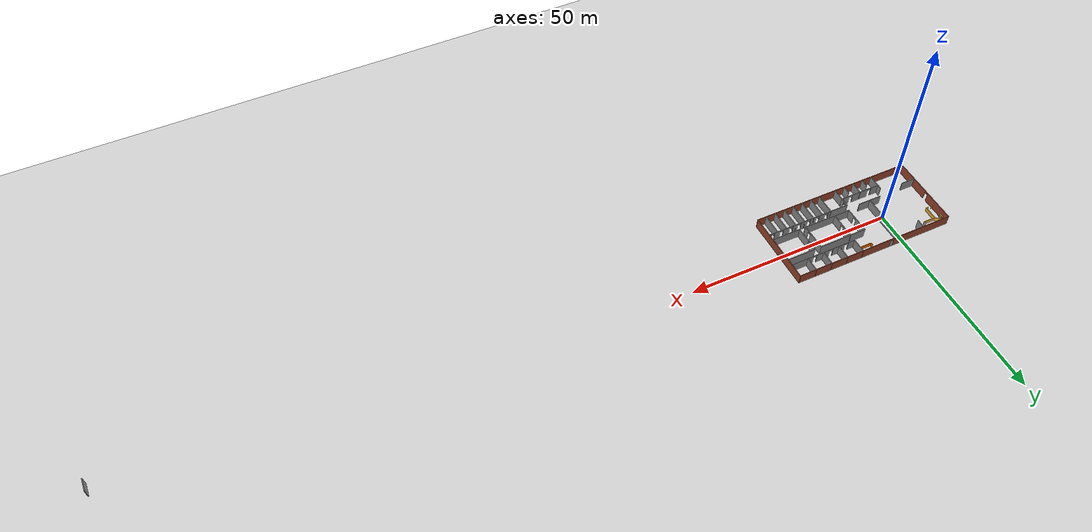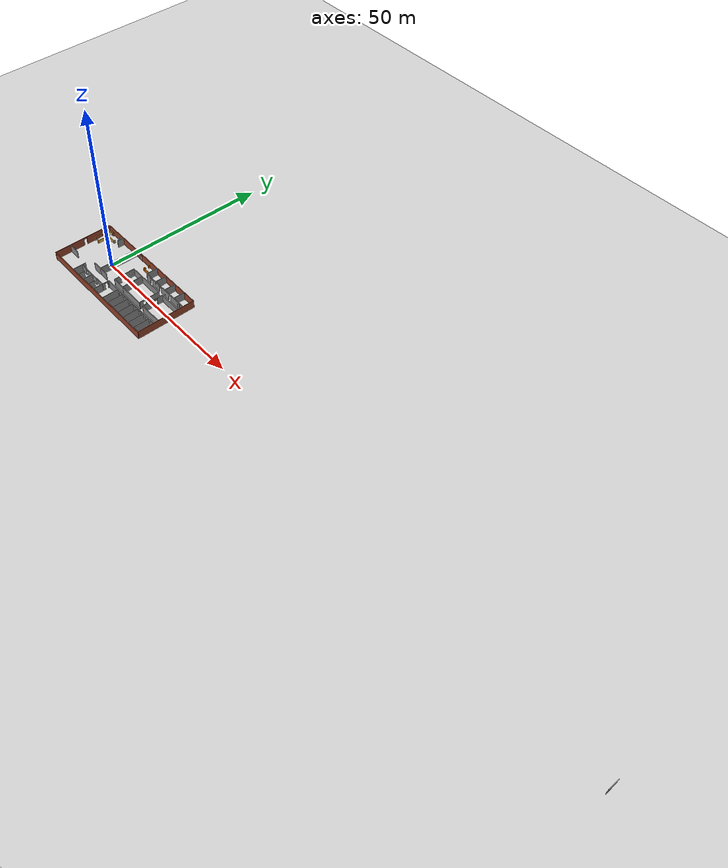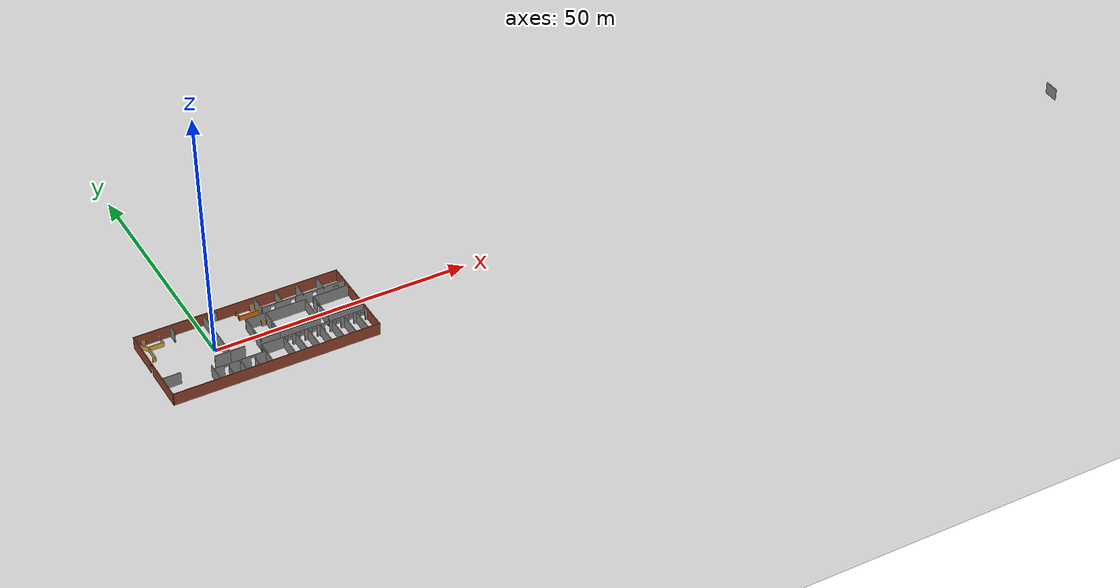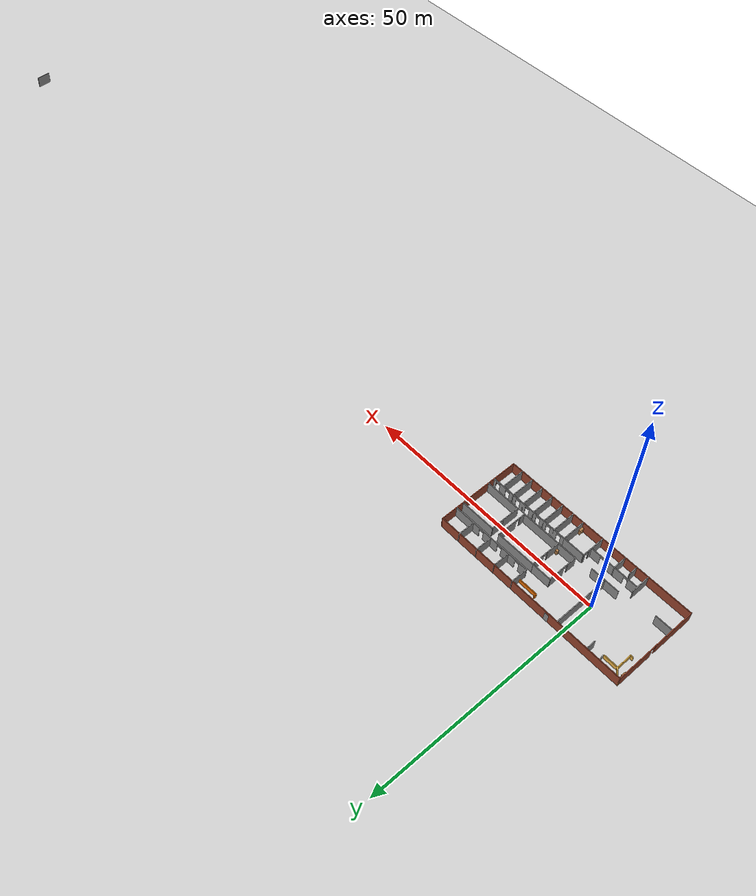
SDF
<sdf version="1.6">
 <world name="default">
  <light name="sun" type="directional">
   <pose>0 0 10 0 -0 0</pose>
   <diffuse>0.8 0.8 0.8 1</diffuse>
   <specular>0.2 0.2 0.2 1</specular>
   <attenuation>
    <range>1000</range>
    <constant>0.9</constant>
    <linear>0.01</linear>
    <quadratic>0.001</quadratic>
   </attenuation>
   <direction>-0.5 0.1 -0.9</direction>
  </light>
  <model name="ground_plane">
   <static>1</static>
   <link name="link">
    <collision name="collision">
     <geometry><plane><normal>0 0 1</normal><size>100 100</size></plane></geometry>
     <surface>
      <contact><collide_bitmask>65535</collide_bitmask></contact>
      <friction><ode><mu>100</mu><mu2>50</mu2></ode></friction>
     </surface>
    </collision>
    <visual name="visual">
     <cast_shadows>0</cast_shadows>
     <geometry><plane><normal>0 0 1</normal><size>100 100</size></plane></geometry>
     <material>
      <script><uri>file://media/materials/scripts/gazebo.material</uri><name>Gazebo/Grey</name></script>
     </material>
    </visual>
   </link>
  </model>
  <gravity>0 0 -9.8</gravity>
  <magnetic_field>6e-06 2.3e-05 -4.2e-05</magnetic_field>
  <atmosphere type="adiabatic"/>
  <physics name="default_physics" default="0" type="ode">
   <max_step_size>0.001</max_step_size>
   <real_time_factor>1</real_time_factor>
   <real_time_update_rate>1000</real_time_update_rate>
  </physics>
  <scene><ambient>0.4 0.4 0.4 1</ambient><background>0.7 0.7 0.7 1</background><shadows>1</shadows></scene>
  <spherical_coordinates>
   <surface_model>EARTH_WGS84</surface_model>
   <latitude_deg>0</latitude_deg>
   <longitude_deg>0</longitude_deg>
   <elevation>0</elevation>
   <heading_deg>0</heading_deg>
  </spherical_coordinates>
  <model name="ER_planfloor">
   <pose>82.8975 -1.25959 0 0 -0 0</pose>
   <link name="Door_36">
    <collision name="Door_36_Collision">
     <geometry><box><size>0.9 0.17 2</size></box></geometry>
     <pose>0 0 1 0 -0 0</pose>
    </collision>
    <visual name="Door_36_Visual">
     <pose>0 0 1 0 -0 0</pose>
     <geometry><box><size>0.9 0.17 2</size></box></geometry>
     <material>
      <script><uri>file://media/materials/scripts/gazebo.material</uri><name>Gazebo/Grey</name></script>
     </material>
    </visual>
    <pose>-57.0688 5.35259 0 0 -0 0</pose>
   </link>
   <link name="Wall_101">
    <pose>-81.0435 -6.03418 0 0 -0 3.14154</pose>
    <visual name="Wall_101_Visual_0">
     <pose>-3.94791 0 1.25 0 -0 0</pose>
     <geometry><box><size>2.10418 0.15 2.5</size></box></geometry>
     <material>
      <script><uri>file://media/materials/scripts/gazebo.material</uri><name>Gazebo/Grey</name></script>
      <ambient>1 1 1 1</ambient>
     </material>
     <meta><layer>0</layer></meta>
    </visual>
    <collision name="Wall_101_Collision_0">
     <geometry><box><size>2.10418 0.15 2.5</size></box></geometry>
     <pose>-3.94791 0 1.25 0 -0 0</pose>
    </collision>
    <visual name="Wall_101_Visual_1">
     <pose>0.101361 0 1.25 0 -0 0</pose>
     <geometry><box><size>4.19437 0.15 2.5</size></box></geometry>
     <material>
      <script><uri>file://media/materials/scripts/gazebo.material</uri><name>Gazebo/Grey</name></script>
      <ambient>1 1 1 1</ambient>
     </material>
     <meta><layer>0</layer></meta>
    </visual>
    <collision name="Wall_101_Collision_1">
     <geometry><box><size>4.19437 0.15 2.5</size></box></geometry>
     <pose>0.101361 0 1.25 0 -0 0</pose>
    </collision>
    <visual name="Wall_101_Visual_2">
     <pose>4.04927 0 1.25 0 -0 0</pose>
     <geometry><box><size>1.90145 0.15 2.5</size></box></geometry>
     <material>
      <script><uri>file://media/materials/scripts/gazebo.material</uri><name>Gazebo/Grey</name></script>
      <ambient>1 1 1 1</ambient>
     </material>
     <meta><layer>0</layer></meta>
    </visual>
    <collision name="Wall_101_Collision_2">
     <geometry><box><size>1.90145 0.15 2.5</size></box></geometry>
     <pose>4.04927 0 1.25 0 -0 0</pose>
    </collision>
    <visual name="Wall_101_Visual_3">
     <pose>-2.44582 0 2.25 0 -0 0</pose>
     <geometry><box><size>0.9 0.15 0.5</size></box></geometry>
     <material>
      <script><uri>file://media/materials/scripts/gazebo.material</uri><name>Gazebo/Grey</name></script>
      <ambient>1 1 1 1</ambient>
     </material>
     <meta><layer>0</layer></meta>
    </visual>
    <collision name="Wall_101_Collision_3">
     <geometry><box><size>0.9 0.15 0.5</size></box></geometry>
     <pose>-2.44582 0 2.25 0 -0 0</pose>
    </collision>
    <visual name="Wall_101_Visual_4">
     <pose>2.64855 0 2.25 0 -0 0</pose>
     <geometry><box><size>0.9 0.15 0.5</size></box></geometry>
     <material>
      <script><uri>file://media/materials/scripts/gazebo.material</uri><name>Gazebo/Grey</name></script>
      <ambient>1 1 1 1</ambient>
     </material>
     <meta><layer>0</layer></meta>
    </visual>
    <collision name="Wall_101_Collision_4">
     <geometry><box><size>0.9 0.15 0.5</size></box></geometry>
     <pose>2.64855 0 2.25 0 -0 0</pose>
    </collision>
   </link>
   <link name="Wall_107">
    <collision name="Wall_107_Collision">
     <geometry><box><size>4.545 0.15 2.5</size></box></geometry>
     <pose>0 0 1.25 0 -0 0</pose>
    </collision>
    <visual name="Wall_107_Visual">
     <pose>0 0 1.25 0 -0 0</pose>
     <geometry><box><size>4.545 0.15 2.5</size></box></geometry>
     <material>
      <script><uri>file://media/materials/scripts/gazebo.material</uri><name>Gazebo/Grey</name></script>
      <ambient>1 1 1 1</ambient>
     </material>
     <meta><layer>0</layer></meta>
    </visual>
    <pose>-73.921 -3.97741 0 0 -0 -0.001365</pose>
   </link>
   <link name="Wall_111">
    <pose>-76.1185 -5.00441 0 0 -0 1.5708</pose>
    <visual name="Wall_111_Visual_0">
     <pose>-0.69229 0 1.25 0 -0 0</pose>
     <geometry><box><size>0.82542 0.15 2.5</size></box></geometry>
     <material>
      <script><uri>file://media/materials/scripts/gazebo.material</uri><name>Gazebo/Grey</name></script>
      <ambient>1 1 1 1</ambient>
     </material>
     <meta><layer>0</layer></meta>
    </visual>
    <collision name="Wall_111_Collision_0">
     <geometry><box><size>0.82542 0.15 2.5</size></box></geometry>
     <pose>-0.69229 0 1.25 0 -0 0</pose>
    </collision>
    <visual name="Wall_111_Visual_1">
     <pose>0.86271 0 1.25 0 -0 0</pose>
     <geometry><box><size>0.48458 0.15 2.5</size></box></geometry>
     <material>
      <script><uri>file://media/materials/scripts/gazebo.material</uri><name>Gazebo/Grey</name></script>
      <ambient>1 1 1 1</ambient>
     </material>
     <meta><layer>0</layer></meta>
    </visual>
    <collision name="Wall_111_Collision_1">
     <geometry><box><size>0.48458 0.15 2.5</size></box></geometry>
     <pose>0.86271 0 1.25 0 -0 0</pose>
    </collision>
    <visual name="Wall_111_Visual_2">
     <pose>0.17042 0 2.25 0 -0 0</pose>
     <geometry><box><size>0.9 0.15 0.5</size></box></geometry>
     <material>
      <script><uri>file://media/materials/scripts/gazebo.material</uri><name>Gazebo/Grey</name></script>
      <ambient>1 1 1 1</ambient>
     </material>
     <meta><layer>0</layer></meta>
    </visual>
    <collision name="Wall_111_Collision_2">
     <geometry><box><size>0.9 0.15 0.5</size></box></geometry>
     <pose>0.17042 0 2.25 0 -0 0</pose>
    </collision>
   </link>
   <link name="Wall_113">
    <pose>-63.5485 -3.98041 0 0 -0 0</pose>
    <visual name="Wall_113_Visual_0">
     <pose>-7.84622 0 1.25 0 -0 0</pose>
     <geometry><box><size>0.807558 0.15 2.5</size></box></geometry>
     <material>
      <script><uri>file://media/materials/scripts/gazebo.material</uri><name>Gazebo/Grey</name></script>
      <ambient>1 1 1 1</ambient>
     </material>
     <meta><layer>0</layer></meta>
    </visual>
    <collision name="Wall_113_Collision_0">
     <geometry><box><size>0.807558 0.15 2.5</size></box></geometry>
     <pose>-7.84622 0 1.25 0 -0 0</pose>
    </collision>
    <visual name="Wall_113_Visual_1">
     <pose>-5.79934 0 1.25 0 -0 0</pose>
     <geometry><box><size>1.48619 0.15 2.5</size></box></geometry>
     <material>
      <script><uri>file://media/materials/scripts/gazebo.material</uri><name>Gazebo/Grey</name></script>
      <ambient>1 1 1 1</ambient>
     </material>
     <meta><layer>0</layer></meta>
    </visual>
    <collision name="Wall_113_Collision_1">
     <geometry><box><size>1.48619 0.15 2.5</size></box></geometry>
     <pose>-5.79934 0 1.25 0 -0 0</pose>
    </collision>
    <visual name="Wall_113_Visual_2">
     <pose>-3.41315 0 1.25 0 -0 0</pose>
     <geometry><box><size>1.48619 0.15 2.5</size></box></geometry>
     <material>
      <script><uri>file://media/materials/scripts/gazebo.material</uri><name>Gazebo/Grey</name></script>
      <ambient>1 1 1 1</ambient>
     </material>
     <meta><layer>0</layer></meta>
    </visual>
    <collision name="Wall_113_Collision_2">
     <geometry><box><size>1.48619 0.15 2.5</size></box></geometry>
     <pose>-3.41315 0 1.25 0 -0 0</pose>
    </collision>
    <visual name="Wall_113_Visual_3">
     <pose>-0.956777 0 1.25 0 -0 0</pose>
     <geometry><box><size>1.62656 0.15 2.5</size></box></geometry>
     <material>
      <script><uri>file://media/materials/scripts/gazebo.material</uri><name>Gazebo/Grey</name></script>
      <ambient>1 1 1 1</ambient>
     </material>
     <meta><layer>0</layer></meta>
    </visual>
    <collision name="Wall_113_Collision_3">
     <geometry><box><size>1.62656 0.15 2.5</size></box></geometry>
     <pose>-0.956777 0 1.25 0 -0 0</pose>
    </collision>
    <visual name="Wall_113_Visual_4">
     <pose>1.40611 0 1.25 0 -0 0</pose>
     <geometry><box><size>1.29921 0.15 2.5</size></box></geometry>
     <material>
      <script><uri>file://media/materials/scripts/gazebo.material</uri><name>Gazebo/Grey</name></script>
      <ambient>1 1 1 1</ambient>
     </material>
     <meta><layer>0</layer></meta>
    </visual>
    <collision name="Wall_113_Collision_4">
     <geometry><box><size>1.29921 0.15 2.5</size></box></geometry>
     <pose>1.40611 0 1.25 0 -0 0</pose>
    </collision>
    <visual name="Wall_113_Visual_5">
     <pose>3.76891 0 1.25 0 -0 0</pose>
     <geometry><box><size>1.62639 0.15 2.5</size></box></geometry>
     <material>
      <script><uri>file://media/materials/scripts/gazebo.material</uri><name>Gazebo/Grey</name></script>
      <ambient>1 1 1 1</ambient>
     </material>
     <meta><layer>0</layer></meta>
    </visual>
    <collision name="Wall_113_Collision_5">
     <geometry><box><size>1.62639 0.15 2.5</size></box></geometry>
     <pose>3.76891 0 1.25 0 -0 0</pose>
    </collision>
    <visual name="Wall_113_Visual_6">
     <pose>6.17841 0 1.25 0 -0 0</pose>
     <geometry><box><size>1.39262 0.15 2.5</size></box></geometry>
     <material>
      <script><uri>file://media/materials/scripts/gazebo.material</uri><name>Gazebo/Grey</name></script>
      <ambient>1 1 1 1</ambient>
     </material>
     <meta><layer>0</layer></meta>
    </visual>
    <collision name="Wall_113_Collision_6">
     <geometry><box><size>1.39262 0.15 2.5</size></box></geometry>
     <pose>6.17841 0 1.25 0 -0 0</pose>
    </collision>
    <visual name="Wall_113_Visual_7">
     <pose>8.01236 0 1.25 0 -0 0</pose>
     <geometry><box><size>0.475282 0.15 2.5</size></box></geometry>
     <material>
      <script><uri>file://media/materials/scripts/gazebo.material</uri><name>Gazebo/Grey</name></script>
      <ambient>1 1 1 1</ambient>
     </material>
     <meta><layer>0</layer></meta>
    </visual>
    <collision name="Wall_113_Collision_7">
     <geometry><box><size>0.475282 0.15 2.5</size></box></geometry>
     <pose>8.01236 0 1.25 0 -0 0</pose>
    </collision>
    <visual name="Wall_113_Visual_8">
     <pose>-6.99244 0 2.25 0 -0 0</pose>
     <geometry><box><size>0.9 0.15 0.5</size></box></geometry>
     <material>
      <script><uri>file://media/materials/scripts/gazebo.material</uri><name>Gazebo/Grey</name></script>
      <ambient>1 1 1 1</ambient>
     </material>
     <meta><layer>0</layer></meta>
    </visual>
    <collision name="Wall_113_Collision_8">
     <geometry><box><size>0.9 0.15 0.5</size></box></geometry>
     <pose>-6.99244 0 2.25 0 -0 0</pose>
    </collision>
    <visual name="Wall_113_Visual_9">
     <pose>-4.60625 0 2.25 0 -0 0</pose>
     <geometry><box><size>0.9 0.15 0.5</size></box></geometry>
     <material>
      <script><uri>file://media/materials/scripts/gazebo.material</uri><name>Gazebo/Grey</name></script>
      <ambient>1 1 1 1</ambient>
     </material>
     <meta><layer>0</layer></meta>
    </visual>
    <collision name="Wall_113_Collision_9">
     <geometry><box><size>0.9 0.15 0.5</size></box></geometry>
     <pose>-4.60625 0 2.25 0 -0 0</pose>
    </collision>
    <visual name="Wall_113_Visual_10">
     <pose>-2.22005 0 2.25 0 -0 0</pose>
     <geometry><box><size>0.9 0.15 0.5</size></box></geometry>
     <material>
      <script><uri>file://media/materials/scripts/gazebo.material</uri><name>Gazebo/Grey</name></script>
      <ambient>1 1 1 1</ambient>
     </material>
     <meta><layer>0</layer></meta>
    </visual>
    <collision name="Wall_113_Collision_10">
     <geometry><box><size>0.9 0.15 0.5</size></box></geometry>
     <pose>-2.22005 0 2.25 0 -0 0</pose>
    </collision>
    <visual name="Wall_113_Visual_11">
     <pose>0.306501 0 2.25 0 -0 0</pose>
     <geometry><box><size>0.9 0.15 0.5</size></box></geometry>
     <material>
      <script><uri>file://media/materials/scripts/gazebo.material</uri><name>Gazebo/Grey</name></script>
      <ambient>1 1 1 1</ambient>
     </material>
     <meta><layer>0</layer></meta>
    </visual>
    <collision name="Wall_113_Collision_11">
     <geometry><box><size>0.9 0.15 0.5</size></box></geometry>
     <pose>0.306501 0 2.25 0 -0 0</pose>
    </collision>
    <visual name="Wall_113_Visual_12">
     <pose>2.50571 0 2.25 0 -0 0</pose>
     <geometry><box><size>0.9 0.15 0.5</size></box></geometry>
     <material>
      <script><uri>file://media/materials/scripts/gazebo.material</uri><name>Gazebo/Grey</name></script>
      <ambient>1 1 1 1</ambient>
     </material>
     <meta><layer>0</layer></meta>
    </visual>
    <collision name="Wall_113_Collision_12">
     <geometry><box><size>0.9 0.15 0.5</size></box></geometry>
     <pose>2.50571 0 2.25 0 -0 0</pose>
    </collision>
    <visual name="Wall_113_Visual_13">
     <pose>5.0321 0 2.25 0 -0 0</pose>
     <geometry><box><size>0.9 0.15 0.5</size></box></geometry>
     <material>
      <script><uri>file://media/materials/scripts/gazebo.material</uri><name>Gazebo/Grey</name></script>
      <ambient>1 1 1 1</ambient>
     </material>
     <meta><layer>0</layer></meta>
    </visual>
    <collision name="Wall_113_Collision_13">
     <geometry><box><size>0.9 0.15 0.5</size></box></geometry>
     <pose>5.0321 0 2.25 0 -0 0</pose>
    </collision>
    <visual name="Wall_113_Visual_14">
     <pose>7.32472 0 2.25 0 -0 0</pose>
     <geometry><box><size>0.9 0.15 0.5</size></box></geometry>
     <material>
      <script><uri>file://media/materials/scripts/gazebo.material</uri><name>Gazebo/Grey</name></script>
      <ambient>1 1 1 1</ambient>
     </material>
     <meta><layer>0</layer></meta>
    </visual>
    <collision name="Wall_113_Collision_14">
     <geometry><box><size>0.9 0.15 0.5</size></box></geometry>
     <pose>7.32472 0 2.25 0 -0 0</pose>
    </collision>
   </link>
   <link name="Wall_115">
    <collision name="Wall_115_Collision">
     <geometry><box><size>5.053 0.15 2.5</size></box></geometry>
     <pose>0 0 1.25 0 -0 0</pose>
    </collision>
    <visual name="Wall_115_Visual">
     <pose>0 0 1.25 0 -0 0</pose>
     <geometry><box><size>5.053 0.15 2.5</size></box></geometry>
     <material>
      <script><uri>file://media/materials/scripts/gazebo.material</uri><name>Gazebo/Grey</name></script>
      <ambient>1 1 1 1</ambient>
     </material>
     <meta><layer>0</layer></meta>
    </visual>
    <pose>-69.4235 -6.43191 0 0 -0 1.5708</pose>
   </link>
   <link name="Wall_119">
    <collision name="Wall_119_Collision">
     <geometry><box><size>5.053 0.15 2.5</size></box></geometry>
     <pose>0 0 1.25 0 -0 0</pose>
    </collision>
    <visual name="Wall_119_Visual">
     <pose>0 0 1.25 0 -0 0</pose>
     <geometry><box><size>5.053 0.15 2.5</size></box></geometry>
     <material>
      <script><uri>file://media/materials/scripts/gazebo.material</uri><name>Gazebo/Grey</name></script>
      <ambient>1 1 1 1</ambient>
     </material>
     <meta><layer>0</layer></meta>
    </visual>
    <pose>-67.0235 -6.43191 0 0 -0 1.5708</pose>
   </link>
   <link name="Wall_123">
    <collision name="Wall_123_Collision">
     <geometry><box><size>5.053 0.15 2.5</size></box></geometry>
     <pose>0 0 1.25 0 -0 0</pose>
    </collision>
    <visual name="Wall_123_Visual">
     <pose>0 0 1.25 0 -0 0</pose>
     <geometry><box><size>5.053 0.15 2.5</size></box></geometry>
     <material>
      <script><uri>file://media/materials/scripts/gazebo.material</uri><name>Gazebo/Grey</name></script>
      <ambient>1 1 1 1</ambient>
     </material>
     <meta><layer>0</layer></meta>
    </visual>
    <pose>-64.6235 -6.43191 0 0 -0 1.5708</pose>
   </link>
   <link name="Wall_125">
    <collision name="Wall_125_Collision">
     <geometry><box><size>5.053 0.15 2.5</size></box></geometry>
     <pose>0 0 1.25 0 -0 0</pose>
    </collision>
    <visual name="Wall_125_Visual">
     <pose>0 0 1.25 0 -0 0</pose>
     <geometry><box><size>5.053 0.15 2.5</size></box></geometry>
     <material>
      <script><uri>file://media/materials/scripts/gazebo.material</uri><name>Gazebo/Grey</name></script>
      <ambient>1 1 1 1</ambient>
     </material>
     <meta><layer>0</layer></meta>
    </visual>
    <pose>-62.2235 -6.43191 0 0 -0 1.5708</pose>
   </link>
   <link name="Wall_127">
    <collision name="Wall_127_Collision">
     <geometry><box><size>5.053 0.15 2.5</size></box></geometry>
     <pose>0 0 1.25 0 -0 0</pose>
    </collision>
    <visual name="Wall_127_Visual">
     <pose>0 0 1.25 0 -0 0</pose>
     <geometry><box><size>5.053 0.15 2.5</size></box></geometry>
     <material>
      <script><uri>file://media/materials/scripts/gazebo.material</uri><name>Gazebo/Grey</name></script>
      <ambient>1 1 1 1</ambient>
     </material>
     <meta><layer>0</layer></meta>
    </visual>
    <pose>-59.8235 -6.43191 0 0 -0 1.5708</pose>
   </link>
   <link name="Wall_133">
    <collision name="Wall_133_Collision">
     <geometry><box><size>5.053 0.15 2.5</size></box></geometry>
     <pose>0 0 1.25 0 -0 0</pose>
    </collision>
    <visual name="Wall_133_Visual">
     <pose>0 0 1.25 0 -0 0</pose>
     <geometry><box><size>5.053 0.15 2.5</size></box></geometry>
     <material>
      <script><uri>file://media/materials/scripts/gazebo.material</uri><name>Gazebo/Grey</name></script>
      <ambient>1 1 1 1</ambient>
     </material>
     <meta><layer>0</layer></meta>
    </visual>
    <pose>-57.4235 -6.43191 0 0 -0 1.5708</pose>
   </link>
   <link name="Wall_135">
    <pose>-71.7235 0.75059 0 0 -0 1.5708</pose>
    <visual name="Wall_135_Visual_0">
     <pose>-1.83958 0 1.25 0 -0 0</pose>
     <geometry><box><size>2.72083 0.15 2.5</size></box></geometry>
     <material>
      <script><uri>file://media/materials/scripts/gazebo.material</uri><name>Gazebo/Grey</name></script>
      <ambient>1 1 1 1</ambient>
     </material>
     <meta><layer>0</layer></meta>
    </visual>
    <collision name="Wall_135_Collision_0">
     <geometry><box><size>2.72083 0.15 2.5</size></box></geometry>
     <pose>-1.83958 0 1.25 0 -0 0</pose>
    </collision>
    <visual name="Wall_135_Visual_1">
     <pose>1.81042 0 1.25 0 -0 0</pose>
     <geometry><box><size>2.77917 0.15 2.5</size></box></geometry>
     <material>
      <script><uri>file://media/materials/scripts/gazebo.material</uri><name>Gazebo/Grey</name></script>
      <ambient>1 1 1 1</ambient>
     </material>
     <meta><layer>0</layer></meta>
    </visual>
    <collision name="Wall_135_Collision_1">
     <geometry><box><size>2.77917 0.15 2.5</size></box></geometry>
     <pose>1.81042 0 1.25 0 -0 0</pose>
    </collision>
    <visual name="Wall_135_Visual_2">
     <pose>-0.029168 0 2.25 0 -0 0</pose>
     <geometry><box><size>0.9 0.15 0.5</size></box></geometry>
     <material>
      <script><uri>file://media/materials/scripts/gazebo.material</uri><name>Gazebo/Grey</name></script>
      <ambient>1 1 1 1</ambient>
     </material>
     <meta><layer>0</layer></meta>
    </visual>
    <collision name="Wall_135_Collision_2">
     <geometry><box><size>0.9 0.15 0.5</size></box></geometry>
     <pose>-0.029168 0 2.25 0 -0 0</pose>
    </collision>
   </link>
   <link name="Wall_143">
    <collision name="Wall_143_Collision">
     <geometry><box><size>3.595 0.15 2.5</size></box></geometry>
     <pose>0 0 1.25 0 -0 0</pose>
    </collision>
    <visual name="Wall_143_Visual">
     <pose>0 0 1.25 0 -0 0</pose>
     <geometry><box><size>3.595 0.15 2.5</size></box></geometry>
     <material>
      <script><uri>file://media/materials/scripts/gazebo.material</uri><name>Gazebo/Grey</name></script>
      <ambient>1 1 1 1</ambient>
     </material>
     <meta><layer>0</layer></meta>
    </visual>
    <pose>-71.7235 7.19809 0 0 -0 1.5708</pose>
   </link>
   <link name="Wall_145">
    <collision name="Wall_145_Collision">
     <geometry><box><size>4 0.15 2.5</size></box></geometry>
     <pose>0 0 1.25 0 -0 0</pose>
    </collision>
    <visual name="Wall_145_Visual">
     <pose>0 0 1.25 0 -0 0</pose>
     <geometry><box><size>4 0.15 2.5</size></box></geometry>
     <material>
      <script><uri>file://media/materials/scripts/gazebo.material</uri><name>Gazebo/Grey</name></script>
      <ambient>1 1 1 1</ambient>
     </material>
     <meta><layer>0</layer></meta>
    </visual>
    <pose>-73.6485 3.87559 0 0 -0 3.14159</pose>
   </link>
   <link name="Wall_146">
    <pose>-75.5735 0.70059 0 0 -0 -1.5708</pose>
    <visual name="Wall_146_Visual_0">
     <pose>-1.48894 0 1.25 0 -0 0</pose>
     <geometry><box><size>3.52212 0.15 2.5</size></box></geometry>
     <material>
      <script><uri>file://media/materials/scripts/gazebo.material</uri><name>Gazebo/Grey</name></script>
      <ambient>1 1 1 1</ambient>
     </material>
     <meta><layer>0</layer></meta>
    </visual>
    <collision name="Wall_146_Collision_0">
     <geometry><box><size>3.52212 0.15 2.5</size></box></geometry>
     <pose>-1.48894 0 1.25 0 -0 0</pose>
    </collision>
    <visual name="Wall_146_Visual_1">
     <pose>2.21106 0 1.25 0 -0 0</pose>
     <geometry><box><size>2.07788 0.15 2.5</size></box></geometry>
     <material>
      <script><uri>file://media/materials/scripts/gazebo.material</uri><name>Gazebo/Grey</name></script>
      <ambient>1 1 1 1</ambient>
     </material>
     <meta><layer>0</layer></meta>
    </visual>
    <collision name="Wall_146_Collision_1">
     <geometry><box><size>2.07788 0.15 2.5</size></box></geometry>
     <pose>2.21106 0 1.25 0 -0 0</pose>
    </collision>
    <visual name="Wall_146_Visual_2">
     <pose>0.722117 0 2.25 0 -0 0</pose>
     <geometry><box><size>0.9 0.15 0.5</size></box></geometry>
     <material>
      <script><uri>file://media/materials/scripts/gazebo.material</uri><name>Gazebo/Grey</name></script>
      <ambient>1 1 1 1</ambient>
     </material>
     <meta><layer>0</layer></meta>
    </visual>
    <collision name="Wall_146_Collision_2">
     <geometry><box><size>0.9 0.15 0.5</size></box></geometry>
     <pose>0.722117 0 2.25 0 -0 0</pose>
    </collision>
   </link>
   <link name="Wall_147">
    <collision name="Wall_147_Collision">
     <geometry><box><size>4 0.15 2.5</size></box></geometry>
     <pose>0 0 1.25 0 -0 0</pose>
    </collision>
    <visual name="Wall_147_Visual">
     <pose>0 0 1.25 0 -0 0</pose>
     <geometry><box><size>4 0.15 2.5</size></box></geometry>
     <material>
      <script><uri>file://media/materials/scripts/gazebo.material</uri><name>Gazebo/Grey</name></script>
      <ambient>1 1 1 1</ambient>
     </material>
     <meta><layer>0</layer></meta>
    </visual>
    <pose>-73.6485 -2.47441 0 0 -0 0</pose>
   </link>
   <link name="Wall_149">
    <collision name="Wall_149_Collision">
     <geometry><box><size>3.916 0.15 1</size></box></geometry>
     <pose>0 0 0.5 0 -0 0</pose>
    </collision>
    <visual name="Wall_149_Visual">
     <pose>0 0 0.5 0 -0 0</pose>
     <geometry><box><size>3.916 0.15 1</size></box></geometry>
     <material>
      <script><uri>file://media/materials/scripts/gazebo.material</uri><name>Gazebo/Grey</name></script>
      <ambient>0.996078 0.47451 0.0196078 1</ambient>
     </material>
     <meta><layer>0</layer></meta>
    </visual>
    <pose>-73.6905 6.90959 0 0 -0 3.14159</pose>
   </link>
   <link name="Wall_151">
    <pose>-75.5735 7.83459 0 0 -0 1.5708</pose>
    <visual name="Wall_151_Visual_0">
     <pose>-0.655933 0 0.5 0 -0 0</pose>
     <geometry><box><size>0.688134 0.15 1</size></box></geometry>
     <material>
      <script><uri>file://media/materials/scripts/gazebo.material</uri><name>Gazebo/Grey</name></script>
      <ambient>0.996078 0.47451 0.0196078 1</ambient>
     </material>
     <meta><layer>0</layer></meta>
    </visual>
    <collision name="Wall_151_Collision_0">
     <geometry><box><size>0.688134 0.15 1</size></box></geometry>
     <pose>-0.655933 0 0.5 0 -0 0</pose>
    </collision>
    <visual name="Wall_151_Visual_1">
     <pose>0.794067 0 0.5 0 -0 0</pose>
     <geometry><box><size>0.411866 0.15 1</size></box></geometry>
     <material>
      <script><uri>file://media/materials/scripts/gazebo.material</uri><name>Gazebo/Grey</name></script>
      <ambient>0.996078 0.47451 0.0196078 1</ambient>
     </material>
     <meta><layer>0</layer></meta>
    </visual>
    <collision name="Wall_151_Collision_1">
     <geometry><box><size>0.411866 0.15 1</size></box></geometry>
     <pose>0.794067 0 0.5 0 -0 0</pose>
    </collision>
   </link>
   <link name="Wall_153">
    <collision name="Wall_153_Collision">
     <geometry><box><size>8 0.15 2.5</size></box></geometry>
     <pose>0 0 1.25 0 -0 0</pose>
    </collision>
    <visual name="Wall_153_Visual">
     <pose>0 0 1.25 0 -0 0</pose>
     <geometry><box><size>8 0.15 2.5</size></box></geometry>
     <material>
      <script><uri>file://media/materials/scripts/gazebo.material</uri><name>Gazebo/Grey</name></script>
      <ambient>1 1 1 1</ambient>
     </material>
     <meta><layer>0</layer></meta>
    </visual>
    <pose>-67.7985 3.87559 0 0 -0 0</pose>
   </link>
   <link name="Wall_156">
    <pose>-63.8735 0.70059 0 0 -0 -1.5708</pose>
    <visual name="Wall_156_Visual_0">
     <pose>-1.08798 0 1.25 0 -0 0</pose>
     <geometry><box><size>4.32403 0.15 2.5</size></box></geometry>
     <material>
      <script><uri>file://media/materials/scripts/gazebo.material</uri><name>Gazebo/Grey</name></script>
      <ambient>1 1 1 1</ambient>
     </material>
     <meta><layer>0</layer></meta>
    </visual>
    <collision name="Wall_156_Collision_0">
     <geometry><box><size>4.32403 0.15 2.5</size></box></geometry>
     <pose>-1.08798 0 1.25 0 -0 0</pose>
    </collision>
    <visual name="Wall_156_Visual_1">
     <pose>2.61201 0 1.25 0 -0 0</pose>
     <geometry><box><size>1.27597 0.15 2.5</size></box></geometry>
     <material>
      <script><uri>file://media/materials/scripts/gazebo.material</uri><name>Gazebo/Grey</name></script>
      <ambient>1 1 1 1</ambient>
     </material>
     <meta><layer>0</layer></meta>
    </visual>
    <collision name="Wall_156_Collision_1">
     <geometry><box><size>1.27597 0.15 2.5</size></box></geometry>
     <pose>2.61201 0 1.25 0 -0 0</pose>
    </collision>
    <visual name="Wall_156_Visual_2">
     <pose>1.52403 0 2.25 0 -0 0</pose>
     <geometry><box><size>0.9 0.15 0.5</size></box></geometry>
     <material>
      <script><uri>file://media/materials/scripts/gazebo.material</uri><name>Gazebo/Grey</name></script>
      <ambient>1 1 1 1</ambient>
     </material>
     <meta><layer>0</layer></meta>
    </visual>
    <collision name="Wall_156_Collision_2">
     <geometry><box><size>0.9 0.15 0.5</size></box></geometry>
     <pose>1.52403 0 2.25 0 -0 0</pose>
    </collision>
   </link>
   <link name="Wall_157">
    <collision name="Wall_157_Collision">
     <geometry><box><size>8 0.15 2.5</size></box></geometry>
     <pose>0 0 1.25 0 -0 0</pose>
    </collision>
    <visual name="Wall_157_Visual">
     <pose>0 0 1.25 0 -0 0</pose>
     <geometry><box><size>8 0.15 2.5</size></box></geometry>
     <material>
      <script><uri>file://media/materials/scripts/gazebo.material</uri><name>Gazebo/Grey</name></script>
      <ambient>1 1 1 1</ambient>
     </material>
     <meta><layer>0</layer></meta>
    </visual>
    <pose>-67.7985 -2.47441 0 0 -0 3.14159</pose>
   </link>
   <link name="Wall_161">
    <collision name="Wall_161_Collision">
     <geometry><box><size>7.179 0.15 2.5</size></box></geometry>
     <pose>0 0 1.25 0 -0 0</pose>
    </collision>
    <visual name="Wall_161_Visual">
     <pose>0 0 1.25 0 -0 0</pose>
     <geometry><box><size>7.179 0.15 2.5</size></box></geometry>
     <material>
      <script><uri>file://media/materials/scripts/gazebo.material</uri><name>Gazebo/Grey</name></script>
      <ambient>1 1 1 1</ambient>
     </material>
     <meta><layer>0</layer></meta>
    </visual>
    <pose>-58.759 3.87559 0 0 -0 3.14159</pose>
   </link>
   <link name="Wall_162">
    <pose>-62.2735 0.70059 0 0 -0 -1.5708</pose>
    <visual name="Wall_162_Visual_0">
     <pose>-2.32787 0 1.25 0 -0 0</pose>
     <geometry><box><size>1.84426 0.15 2.5</size></box></geometry>
     <material>
      <script><uri>file://media/materials/scripts/gazebo.material</uri><name>Gazebo/Grey</name></script>
      <ambient>1 1 1 1</ambient>
     </material>
     <meta><layer>0</layer></meta>
    </visual>
    <collision name="Wall_162_Collision_0">
     <geometry><box><size>1.84426 0.15 2.5</size></box></geometry>
     <pose>-2.32787 0 1.25 0 -0 0</pose>
    </collision>
    <visual name="Wall_162_Visual_1">
     <pose>1.37213 0 1.25 0 -0 0</pose>
     <geometry><box><size>3.75574 0.15 2.5</size></box></geometry>
     <material>
      <script><uri>file://media/materials/scripts/gazebo.material</uri><name>Gazebo/Grey</name></script>
      <ambient>1 1 1 1</ambient>
     </material>
     <meta><layer>0</layer></meta>
    </visual>
    <collision name="Wall_162_Collision_1">
     <geometry><box><size>3.75574 0.15 2.5</size></box></geometry>
     <pose>1.37213 0 1.25 0 -0 0</pose>
    </collision>
    <visual name="Wall_162_Visual_2">
     <pose>-0.955739 0 2.25 0 -0 0</pose>
     <geometry><box><size>0.9 0.15 0.5</size></box></geometry>
     <material>
      <script><uri>file://media/materials/scripts/gazebo.material</uri><name>Gazebo/Grey</name></script>
      <ambient>1 1 1 1</ambient>
     </material>
     <meta><layer>0</layer></meta>
    </visual>
    <collision name="Wall_162_Collision_2">
     <geometry><box><size>0.9 0.15 0.5</size></box></geometry>
     <pose>-0.955739 0 2.25 0 -0 0</pose>
    </collision>
   </link>
   <link name="Wall_163">
    <collision name="Wall_163_Collision">
     <geometry><box><size>7.179 0.15 2.5</size></box></geometry>
     <pose>0 0 1.25 0 -0 0</pose>
    </collision>
    <visual name="Wall_163_Visual">
     <pose>0 0 1.25 0 -0 0</pose>
     <geometry><box><size>7.179 0.15 2.5</size></box></geometry>
     <material>
      <script><uri>file://media/materials/scripts/gazebo.material</uri><name>Gazebo/Grey</name></script>
      <ambient>1 1 1 1</ambient>
     </material>
     <meta><layer>0</layer></meta>
    </visual>
    <pose>-58.759 -2.48489 0 0 -0 -0.002983</pose>
   </link>
   <link name="Wall_165">
    <pose>-63.5485 5.47559 0 0 -0 0</pose>
    <visual name="Wall_165_Visual_0">
     <pose>-7.37978 0 1.25 0 -0 0</pose>
     <geometry><box><size>1.74045 0.15 2.5</size></box></geometry>
     <material>
      <script><uri>file://media/materials/scripts/gazebo.material</uri><name>Gazebo/Grey</name></script>
      <ambient>1 1 1 1</ambient>
     </material>
     <meta><layer>0</layer></meta>
    </visual>
    <collision name="Wall_165_Collision_0">
     <geometry><box><size>1.74045 0.15 2.5</size></box></geometry>
     <pose>-7.37978 0 1.25 0 -0 0</pose>
    </collision>
    <visual name="Wall_165_Visual_1">
     <pose>-4.02427 0 1.25 0 -0 0</pose>
     <geometry><box><size>3.17056 0.15 2.5</size></box></geometry>
     <material>
      <script><uri>file://media/materials/scripts/gazebo.material</uri><name>Gazebo/Grey</name></script>
      <ambient>1 1 1 1</ambient>
     </material>
     <meta><layer>0</layer></meta>
    </visual>
    <collision name="Wall_165_Collision_1">
     <geometry><box><size>3.17056 0.15 2.5</size></box></geometry>
     <pose>-4.02427 0 1.25 0 -0 0</pose>
    </collision>
    <visual name="Wall_165_Visual_2">
     <pose>0.139872 0 1.25 0 -0 0</pose>
     <geometry><box><size>3.35772 0.15 2.5</size></box></geometry>
     <material>
      <script><uri>file://media/materials/scripts/gazebo.material</uri><name>Gazebo/Grey</name></script>
      <ambient>1 1 1 1</ambient>
     </material>
     <meta><layer>0</layer></meta>
    </visual>
    <collision name="Wall_165_Collision_2">
     <geometry><box><size>3.35772 0.15 2.5</size></box></geometry>
     <pose>0.139872 0 1.25 0 -0 0</pose>
    </collision>
    <visual name="Wall_165_Visual_3">
     <pose>5.48437 0 1.25 0 -0 0</pose>
     <geometry><box><size>5.53127 0.15 2.5</size></box></geometry>
     <material>
      <script><uri>file://media/materials/scripts/gazebo.material</uri><name>Gazebo/Grey</name></script>
      <ambient>1 1 1 1</ambient>
     </material>
     <meta><layer>0</layer></meta>
    </visual>
    <collision name="Wall_165_Collision_3">
     <geometry><box><size>5.53127 0.15 2.5</size></box></geometry>
     <pose>5.48437 0 1.25 0 -0 0</pose>
    </collision>
    <visual name="Wall_165_Visual_4">
     <pose>-6.05955 0 2.25 0 -0 0</pose>
     <geometry><box><size>0.9 0.15 0.5</size></box></geometry>
     <material>
      <script><uri>file://media/materials/scripts/gazebo.material</uri><name>Gazebo/Grey</name></script>
      <ambient>1 1 1 1</ambient>
     </material>
     <meta><layer>0</layer></meta>
    </visual>
    <collision name="Wall_165_Collision_4">
     <geometry><box><size>0.9 0.15 0.5</size></box></geometry>
     <pose>-6.05955 0 2.25 0 -0 0</pose>
    </collision>
    <visual name="Wall_165_Visual_5">
     <pose>-1.98899 0 2.25 0 -0 0</pose>
     <geometry><box><size>0.9 0.15 0.5</size></box></geometry>
     <material>
      <script><uri>file://media/materials/scripts/gazebo.material</uri><name>Gazebo/Grey</name></script>
      <ambient>1 1 1 1</ambient>
     </material>
     <meta><layer>0</layer></meta>
    </visual>
    <collision name="Wall_165_Collision_5">
     <geometry><box><size>0.9 0.15 0.5</size></box></geometry>
     <pose>-1.98899 0 2.25 0 -0 0</pose>
    </collision>
    <visual name="Wall_165_Visual_6">
     <pose>2.26873 0 2.25 0 -0 0</pose>
     <geometry><box><size>0.9 0.15 0.5</size></box></geometry>
     <material>
      <script><uri>file://media/materials/scripts/gazebo.material</uri><name>Gazebo/Grey</name></script>
      <ambient>1 1 1 1</ambient>
     </material>
     <meta><layer>0</layer></meta>
    </visual>
    <collision name="Wall_165_Collision_6">
     <geometry><box><size>0.9 0.15 0.5</size></box></geometry>
     <pose>2.26873 0 2.25 0 -0 0</pose>
    </collision>
   </link>
   <link name="Wall_167">
    <collision name="Wall_167_Collision">
     <geometry><box><size>3.595 0.15 2.5</size></box></geometry>
     <pose>0 0 1.25 0 -0 0</pose>
    </collision>
    <visual name="Wall_167_Visual">
     <pose>0 0 1.25 0 -0 0</pose>
     <geometry><box><size>3.595 0.15 2.5</size></box></geometry>
     <material>
      <script><uri>file://media/materials/scripts/gazebo.material</uri><name>Gazebo/Grey</name></script>
      <ambient>1 1 1 1</ambient>
     </material>
     <meta><layer>0</layer></meta>
    </visual>
    <pose>-67.5985 7.19809 0 0 -0 1.5708</pose>
   </link>
   <link name="Wall_169">
    <collision name="Wall_169_Collision">
     <geometry><box><size>3.595 0.15 2.5</size></box></geometry>
     <pose>0 0 1.25 0 -0 0</pose>
    </collision>
    <visual name="Wall_169_Visual">
     <pose>0 0 1.25 0 -0 0</pose>
     <geometry><box><size>3.595 0.15 2.5</size></box></geometry>
     <material>
      <script><uri>file://media/materials/scripts/gazebo.material</uri><name>Gazebo/Grey</name></script>
      <ambient>1 1 1 1</ambient>
     </material>
     <meta><layer>0</layer></meta>
    </visual>
    <pose>-63.4735 7.19809 0 0 -0 1.5708</pose>
   </link>
   <link name="Wall_171">
    <collision name="Wall_171_Collision">
     <geometry><box><size>3.595 0.15 2.5</size></box></geometry>
     <pose>0 0 1.25 0 -0 0</pose>
    </collision>
    <visual name="Wall_171_Visual">
     <pose>0 0 1.25 0 -0 0</pose>
     <geometry><box><size>3.595 0.15 2.5</size></box></geometry>
     <material>
      <script><uri>file://media/materials/scripts/gazebo.material</uri><name>Gazebo/Grey</name></script>
      <ambient>1 1 1 1</ambient>
     </material>
     <meta><layer>0</layer></meta>
    </visual>
    <pose>-59.3485 7.19809 0 0 -0 1.5708</pose>
   </link>
   <link name="Wall_26">
    <collision name="Wall_26_Collision">
     <geometry><box><size>40 0.15 2.5</size></box></geometry>
     <pose>0 0 1.25 0 -0 0</pose>
    </collision>
    <visual name="Wall_26_Visual">
     <pose>0 0 1.25 0 -0 0</pose>
     <geometry><box><size>40 0.15 2.5</size></box></geometry>
     <material>
      <script><uri>file://media/materials/scripts/gazebo.material</uri><name>Gazebo/Bricks</name></script>
      <ambient>1 1 1 1</ambient>
     </material>
     <meta><layer>0</layer></meta>
    </visual>
    <pose>-75.1465 8.90959 0 0 -0 0</pose>
   </link>
   <link name="Wall_28">
    <collision name="Wall_28_Collision">
     <geometry><box><size>18 0.15 2.5</size></box></geometry>
     <pose>0 0 1.25 0 -0 0</pose>
    </collision>
    <visual name="Wall_28_Visual">
     <pose>0 0 1.25 0 -0 0</pose>
     <geometry><box><size>18 0.15 2.5</size></box></geometry>
     <material>
      <script><uri>file://media/materials/scripts/gazebo.material</uri><name>Gazebo/Bricks</name></script>
      <ambient>1 1 1 1</ambient>
     </material>
     <meta><layer>0</layer></meta>
    </visual>
    <pose>-55.2215 -0.01541 0 0 -0 -1.5708</pose>
   </link>
   <link name="Wall_30">
    <collision name="Wall_30_Collision">
     <geometry><box><size>40 0.15 2.5</size></box></geometry>
     <pose>0 0 1.25 0 -0 0</pose>
    </collision>
    <visual name="Wall_30_Visual">
     <pose>0 0 1.25 0 -0 0</pose>
     <geometry><box><size>40 0.15 2.5</size></box></geometry>
     <material>
      <script><uri>file://media/materials/scripts/gazebo.material</uri><name>Gazebo/Bricks</name></script>
      <ambient>1 1 1 1</ambient>
     </material>
     <meta><layer>0</layer></meta>
    </visual>
    <pose>-75.1465 -8.94041 0 0 -0 3.14159</pose>
   </link>
   <link name="Wall_34">
    <pose>-95.0715 -0.01541 0 0 -0 1.5708</pose>
    <visual name="Wall_34_Visual_0">
     <pose>-4.38317 0 1.25 0 -0 0</pose>
     <geometry><box><size>9.23408 0.15 2.5</size></box></geometry>
     <material>
      <script><uri>file://media/materials/scripts/gazebo.material</uri><name>Gazebo/Bricks</name></script>
      <ambient>1 1 1 1</ambient>
     </material>
     <meta><layer>0</layer></meta>
    </visual>
    <collision name="Wall_34_Collision_0">
     <geometry><box><size>9.23408 0.15 2.5</size></box></geometry>
     <pose>-4.38317 0 1.25 0 -0 0</pose>
    </collision>
    <visual name="Wall_34_Visual_1">
     <pose>5.06704 0 1.25 0 -0 0</pose>
     <geometry><box><size>7.86634 0.15 2.5</size></box></geometry>
     <material>
      <script><uri>file://media/materials/scripts/gazebo.material</uri><name>Gazebo/Bricks</name></script>
      <ambient>1 1 1 1</ambient>
     </material>
     <meta><layer>0</layer></meta>
    </visual>
    <collision name="Wall_34_Collision_1">
     <geometry><box><size>7.86634 0.15 2.5</size></box></geometry>
     <pose>5.06704 0 1.25 0 -0 0</pose>
    </collision>
    <visual name="Wall_34_Visual_2">
     <pose>0.68387 0 2.25 0 -0 0</pose>
     <geometry><box><size>0.9 0.15 0.5</size></box></geometry>
     <material>
      <script><uri>file://media/materials/scripts/gazebo.material</uri><name>Gazebo/Bricks</name></script>
      <ambient>1 1 1 1</ambient>
     </material>
     <meta><layer>0</layer></meta>
    </visual>
    <collision name="Wall_34_Collision_2">
     <geometry><box><size>0.9 0.15 0.5</size></box></geometry>
     <pose>0.68387 0 2.25 0 -0 0</pose>
    </collision>
   </link>
   <link name="Wall_43">
    <pose>-90.307 7.84557 0 0 -0 1.5708</pose>
    <visual name="Wall_43_Visual_0">
     <pose>-0.689526 0 0.5 0 -0 0</pose>
     <geometry><box><size>0.620948 0.15 1</size></box></geometry>
     <material>
      <script><uri>file://media/materials/scripts/gazebo.material</uri><name>Gazebo/CeilingTiled</name></script>
      <ambient>1 0.764706 0.305882 1</ambient>
     </material>
     <meta><layer>0</layer></meta>
    </visual>
    <collision name="Wall_43_Collision_0">
     <geometry><box><size>0.620948 0.15 1</size></box></geometry>
     <pose>-0.689526 0 0.5 0 -0 0</pose>
    </collision>
    <visual name="Wall_43_Visual_1">
     <pose>0.760474 0 0.5 0 -0 0</pose>
     <geometry><box><size>0.479052 0.15 1</size></box></geometry>
     <material>
      <script><uri>file://media/materials/scripts/gazebo.material</uri><name>Gazebo/CeilingTiled</name></script>
      <ambient>1 0.764706 0.305882 1</ambient>
     </material>
     <meta><layer>0</layer></meta>
    </visual>
    <collision name="Wall_43_Collision_1">
     <geometry><box><size>0.479052 0.15 1</size></box></geometry>
     <pose>0.760474 0 0.5 0 -0 0</pose>
    </collision>
   </link>
   <link name="Wall_57">
    <pose>-94.1325 3.69259 0 0 -0 0</pose>
    <visual name="Wall_57_Visual_0">
     <pose>-0.774493 0 0.5 0 -0 0</pose>
     <geometry><box><size>0.451014 0.15 1</size></box></geometry>
     <material>
      <script><uri>file://media/materials/scripts/gazebo.material</uri><name>Gazebo/Grey</name></script>
      <ambient>1 0.764706 0.305882 1</ambient>
     </material>
     <meta><layer>0</layer></meta>
    </visual>
    <collision name="Wall_57_Collision_0">
     <geometry><box><size>0.451014 0.15 1</size></box></geometry>
     <pose>-0.774493 0 0.5 0 -0 0</pose>
    </collision>
    <visual name="Wall_57_Visual_1">
     <pose>0.675507 0 0.5 0 -0 0</pose>
     <geometry><box><size>0.648986 0.15 1</size></box></geometry>
     <material>
      <script><uri>file://media/materials/scripts/gazebo.material</uri><name>Gazebo/Grey</name></script>
      <ambient>1 0.764706 0.305882 1</ambient>
     </material>
     <meta><layer>0</layer></meta>
    </visual>
    <collision name="Wall_57_Collision_1">
     <geometry><box><size>0.648986 0.15 1</size></box></geometry>
     <pose>0.675507 0 0.5 0 -0 0</pose>
    </collision>
   </link>
   <link name="Wall_59">
    <collision name="Wall_59_Collision">
     <geometry><box><size>2.94742 0.15 1</size></box></geometry>
     <pose>0 0 0.5 0 -0 0</pose>
    </collision>
    <visual name="Wall_59_Visual">
     <pose>0 0 0.5 0 -0 0</pose>
     <geometry><box><size>2.94742 0.15 1</size></box></geometry>
     <material>
      <script><uri>file://media/materials/scripts/gazebo.material</uri><name>Gazebo/Grey</name></script>
      <ambient>1 0.764706 0.305882 1</ambient>
     </material>
     <meta><layer>0</layer></meta>
    </visual>
    <pose>-94.1094 7.89436 0 0 -0 -0.812247</pose>
   </link>
   <link name="Wall_65">
    <collision name="Wall_65_Collision">
     <geometry><box><size>3.25 0.15 1</size></box></geometry>
     <pose>0 0 0.5 0 -0 0</pose>
    </collision>
    <visual name="Wall_65_Visual">
     <pose>0 0 0.5 0 -0 0</pose>
     <geometry><box><size>3.25 0.15 1</size></box></geometry>
     <material>
      <script><uri>file://media/materials/scripts/gazebo.material</uri><name>Gazebo/Grey</name></script>
      <ambient>1 0.764706 0.305882 1</ambient>
     </material>
     <meta><layer>0</layer></meta>
    </visual>
    <pose>-93.2075 5.24259 0 0 -0 1.5708</pose>
   </link>
   <link name="Wall_67">
    <collision name="Wall_67_Collision">
     <geometry><box><size>3.02152 0.15 1</size></box></geometry>
     <pose>0 0 0.5 0 -0 0</pose>
    </collision>
    <visual name="Wall_67_Visual">
     <pose>0 0 0.5 0 -0 0</pose>
     <geometry><box><size>3.02152 0.15 1</size></box></geometry>
     <material>
      <script><uri>file://media/materials/scripts/gazebo.material</uri><name>Gazebo/Grey</name></script>
      <ambient>1 0.764706 0.305882 1</ambient>
     </material>
     <meta><layer>0</layer></meta>
    </visual>
    <pose>-91.7424 6.9064 0 0 -0 3.13928</pose>
   </link>
   <link name="Wall_69">
    <collision name="Wall_69_Collision">
     <geometry><box><size>12 0.15 2.5</size></box></geometry>
     <pose>0 0 1.25 0 -0 0</pose>
    </collision>
    <visual name="Wall_69_Visual">
     <pose>0 0 1.25 0 -0 0</pose>
     <geometry><box><size>12 0.15 2.5</size></box></geometry>
     <material>
      <script><uri>file://media/materials/scripts/gazebo.material</uri><name>Gazebo/Grey</name></script>
      <ambient>1 1 1 1</ambient>
     </material>
     <meta><layer>0</layer></meta>
    </visual>
    <pose>-81.7235 2.94959 0 0 -0 -1.5708</pose>
   </link>
   <link name="Wall_71">
    <collision name="Wall_71_Collision">
     <geometry><box><size>3 0.15 2.5</size></box></geometry>
     <pose>0 0 1.25 0 -0 0</pose>
    </collision>
    <visual name="Wall_71_Visual">
     <pose>0 0 1.25 0 -0 0</pose>
     <geometry><box><size>3 0.15 2.5</size></box></geometry>
     <material>
      <script><uri>file://media/materials/scripts/gazebo.material</uri><name>Gazebo/Grey</name></script>
      <ambient>1 1 1 1</ambient>
     </material>
     <meta><layer>0</layer></meta>
    </visual>
    <pose>-83.1485 -2.97541 0 0 -0 3.14159</pose>
   </link>
   <link name="Wall_73">
    <collision name="Wall_73_Collision">
     <geometry><box><size>3 0.15 2.5</size></box></geometry>
     <pose>0 0 1.25 0 -0 0</pose>
    </collision>
    <visual name="Wall_73_Visual">
     <pose>0 0 1.25 0 -0 0</pose>
     <geometry><box><size>3 0.15 2.5</size></box></geometry>
     <material>
      <script><uri>file://media/materials/scripts/gazebo.material</uri><name>Gazebo/Grey</name></script>
      <ambient>1 1 1 1</ambient>
     </material>
     <meta><layer>0</layer></meta>
    </visual>
    <pose>-80.2985 -2.97541 0 0 -0 0</pose>
   </link>
   <link name="Wall_75">
    <collision name="Wall_75_Collision">
     <geometry><box><size>4 0.15 2.5</size></box></geometry>
     <pose>0 0 1.25 0 -0 0</pose>
    </collision>
    <visual name="Wall_75_Visual">
     <pose>0 0 1.25 0 -0 0</pose>
     <geometry><box><size>4 0.15 2.5</size></box></geometry>
     <material>
      <script><uri>file://media/materials/scripts/gazebo.material</uri><name>Gazebo/Grey</name></script>
      <ambient>1 1 1 1</ambient>
     </material>
     <meta><layer>0</layer></meta>
    </visual>
    <pose>-86.1185 -6.95141 0 0 -0 1.5708</pose>
   </link>
   <link name="Wall_79">
    <collision name="Wall_79_Collision">
     <geometry><box><size>3.5 0.15 2.5</size></box></geometry>
     <pose>0 0 1.25 0 -0 0</pose>
    </collision>
    <visual name="Wall_79_Visual">
     <pose>0 0 1.25 0 -0 0</pose>
     <geometry><box><size>3.5 0.15 2.5</size></box></geometry>
     <material>
      <script><uri>file://media/materials/scripts/gazebo.material</uri><name>Gazebo/Grey</name></script>
      <ambient>1 1 1 1</ambient>
     </material>
     <meta><layer>0</layer></meta>
    </visual>
    <pose>-93.3171 -4.12412 0 0 -0 0</pose>
   </link>
   <link name="Wall_81">
    <collision name="Wall_81_Collision">
     <geometry><box><size>2 0.15 2.5</size></box></geometry>
     <pose>0 0 1.25 0 -0 0</pose>
    </collision>
    <visual name="Wall_81_Visual">
     <pose>0 0 1.25 0 -0 0</pose>
     <geometry><box><size>2 0.15 2.5</size></box></geometry>
     <material>
      <script><uri>file://media/materials/scripts/gazebo.material</uri><name>Gazebo/Grey</name></script>
      <ambient>1 1 1 1</ambient>
     </material>
     <meta><layer>0</layer></meta>
    </visual>
    <pose>-88.1011 7.86382 0 0 -0 -1.5708</pose>
   </link>
   <link name="Wall_83">
    <collision name="Wall_83_Collision">
     <geometry><box><size>2 0.15 2.5</size></box></geometry>
     <pose>0 0 1.25 0 -0 0</pose>
    </collision>
    <visual name="Wall_83_Visual">
     <pose>0 0 1.25 0 -0 0</pose>
     <geometry><box><size>2 0.15 2.5</size></box></geometry>
     <material>
      <script><uri>file://media/materials/scripts/gazebo.material</uri><name>Gazebo/Grey</name></script>
      <ambient>1 1 1 1</ambient>
     </material>
     <meta><layer>0</layer></meta>
    </visual>
    <pose>-83.6185 -7.95841 0 0 -0 1.5708</pose>
   </link>
   <link name="Wall_85">
    <collision name="Wall_85_Collision">
     <geometry><box><size>3 0.15 2.5</size></box></geometry>
     <pose>0 0 1.25 0 -0 0</pose>
    </collision>
    <visual name="Wall_85_Visual">
     <pose>0 0 1.25 0 -0 0</pose>
     <geometry><box><size>3 0.15 2.5</size></box></geometry>
     <material>
      <script><uri>file://media/materials/scripts/gazebo.material</uri><name>Gazebo/Grey</name></script>
      <ambient>1 1 1 1</ambient>
     </material>
     <meta><layer>0</layer></meta>
    </visual>
    <pose>-81.1185 -7.45841 0 0 -0 1.5708</pose>
   </link>
   <link name="Wall_87">
    <collision name="Wall_87_Collision">
     <geometry><box><size>3 0.15 2.5</size></box></geometry>
     <pose>0 0 1.25 0 -0 0</pose>
    </collision>
    <visual name="Wall_87_Visual">
     <pose>0 0 1.25 0 -0 0</pose>
     <geometry><box><size>3 0.15 2.5</size></box></geometry>
     <material>
      <script><uri>file://media/materials/scripts/gazebo.material</uri><name>Gazebo/Grey</name></script>
      <ambient>1 1 1 1</ambient>
     </material>
     <meta><layer>0</layer></meta>
    </visual>
    <pose>95.1025 -7.38941 0 0 -0 1.5708</pose>
   </link>
   <link name="Wall_91">
    <collision name="Wall_91_Collision">
     <geometry><box><size>2 0.15 2.5</size></box></geometry>
     <pose>0 0 1.25 0 -0 0</pose>
    </collision>
    <visual name="Wall_91_Visual">
     <pose>0 0 1.25 0 -0 0</pose>
     <geometry><box><size>2 0.15 2.5</size></box></geometry>
     <material>
      <script><uri>file://media/materials/scripts/gazebo.material</uri><name>Gazebo/Grey</name></script>
      <ambient>1 1 1 1</ambient>
     </material>
     <meta><layer>0</layer></meta>
    </visual>
    <pose>-78.6185 -7.95841 0 0 -0 1.5708</pose>
   </link>
   <link name="Wall_97">
    <collision name="Wall_97_Collision">
     <geometry><box><size>5.053 0.15 2.5</size></box></geometry>
     <pose>0 0 1.25 0 -0 0</pose>
    </collision>
    <visual name="Wall_97_Visual">
     <pose>0 0 1.25 0 -0 0</pose>
     <geometry><box><size>5.053 0.15 2.5</size></box></geometry>
     <material>
      <script><uri>file://media/materials/scripts/gazebo.material</uri><name>Gazebo/Grey</name></script>
      <ambient>1 1 1 1</ambient>
     </material>
     <meta><layer>0</layer></meta>
    </visual>
    <pose>-71.7235 -6.43191 0 0 -0 1.5708</pose>
   </link>
   <link name="Wall_99">
    <collision name="Wall_99_Collision">
     <geometry><box><size>2.99947 0.15 2.5</size></box></geometry>
     <pose>0 0 1.25 0 -0 0</pose>
    </collision>
    <visual name="Wall_99_Visual">
     <pose>0 0 1.25 0 -0 0</pose>
     <geometry><box><size>2.99947 0.15 2.5</size></box></geometry>
     <material>
      <script><uri>file://media/materials/scripts/gazebo.material</uri><name>Gazebo/Grey</name></script>
      <ambient>1 1 1 1</ambient>
     </material>
     <meta><layer>0</layer></meta>
    </visual>
    <pose>-76.1185 -7.45891 0 0 -0 1.5708</pose>
   </link>
   <static>1</static>
  </model>
  <model name="ER_Floorplan2">
   <link name="Door_40">
    <collision name="Door_40_Collision">
     <geometry><box><size>0.9 0.17 2</size></box></geometry>
     <pose>0 0 1 0 -0 0</pose>
    </collision>
    <visual name="Door_40_Visual">
     <pose>0 0 1 0 -0 0</pose>
     <geometry><box><size>0.9 0.17 2</size></box></geometry>
     <material>
      <script><uri>file://media/materials/scripts/gazebo.material</uri><name>Gazebo/Grey</name></script>
     </material>
    </visual>
    <pose>3.33147 7.64956 0 0 -0 0</pose>
   </link>
   <static>1</static>
  </model>
  <model name="bookshelf">
   <static>1</static>
   <link name="link">
    <inertial><mass>1</mass></inertial>
    <collision name="back">
     <pose>0 0.005 0.6 0 -0 0</pose>
     <geometry><box><size>0.9 0.01 1.2</size></box></geometry>
    </collision>
    <visual name="visual1">
     <pose>0 0.005 0.6 0 -0 0</pose>
     <geometry><box><size>0.9 0.01 1.2</size></box></geometry>
     <material>
      <script><uri>file://media/materials/scripts/gazebo.material</uri><name>Gazebo/Wood</name></script>
     </material>
    </visual>
    <collision name="left_side">
     <pose>0.45 -0.195 0.6 0 -0 0</pose>
     <geometry><box><size>0.02 0.4 1.2</size></box></geometry>
    </collision>
    <visual name="visual2">
     <pose>0.45 -0.195 0.6 0 -0 0</pose>
     <geometry><box><size>0.02 0.4 1.2</size></box></geometry>
     <material>
      <script><uri>file://media/materials/scripts/gazebo.material</uri><name>Gazebo/Wood</name></script>
     </material>
    </visual>
    <collision name="right_side">
     <pose>-0.45 -0.195 0.6 0 -0 0</pose>
     <geometry><box><size>0.02 0.4 1.2</size></box></geometry>
    </collision>
    <visual name="visual3">
     <pose>-0.45 -0.195 0.6 0 -0 0</pose>
     <geometry><box><size>0.02 0.4 1.2</size></box></geometry>
     <material>
      <script><uri>file://media/materials/scripts/gazebo.material</uri><name>Gazebo/Wood</name></script>
     </material>
    </visual>
    <collision name="bottom">
     <pose>0 -0.195 0.03 0 -0 0</pose>
     <geometry><box><size>0.88 0.4 0.06</size></box></geometry>
    </collision>
    <visual name="visual4">
     <pose>0 -0.195 0.03 0 -0 0</pose>
     <geometry><box><size>0.88 0.4 0.06</size></box></geometry>
     <material>
      <script><uri>file://media/materials/scripts/gazebo.material</uri><name>Gazebo/Wood</name></script>
     </material>
    </visual>
    <collision name="top">
     <pose>0 -0.195 1.19 0 -0 0</pose>
     <geometry><box><size>0.88 0.4 0.02</size></box></geometry>
    </collision>
    <visual name="visual5">
     <pose>0 -0.195 1.19 0 -0 0</pose>
     <geometry><box><size>0.88 0.4 0.02</size></box></geometry>
     <material>
      <script><uri>file://media/materials/scripts/gazebo.material</uri><name>Gazebo/Wood</name></script>
     </material>
    </visual>
    <collision name="low_shelf">
     <pose>0 -0.195 0.43 0 -0 0</pose>
     <geometry><box><size>0.88 0.4 0.02</size></box></geometry>
    </collision>
    <visual name="visual6">
     <pose>0 -0.195 0.43 0 -0 0</pose>
     <geometry><box><size>0.88 0.4 0.02</size></box></geometry>
     <material>
      <script><uri>file://media/materials/scripts/gazebo.material</uri><name>Gazebo/Wood</name></script>
     </material>
    </visual>
    <collision name="high_shelf">
     <pose>0 -0.195 0.8 0 -0 0</pose>
     <geometry><box><size>0.88 0.4 0.02</size></box></geometry>
    </collision>
    <visual name="visual7">
     <pose>0 -0.195 0.8 0 -0 0</pose>
     <geometry><box><size>0.88 0.4 0.02</size></box></geometry>
     <material>
      <script><uri>file://media/materials/scripts/gazebo.material</uri><name>Gazebo/Wood</name></script>
     </material>
    </visual>
   </link>
   <pose>-10.5858 7.54696 0 0 -0 0</pose>
  </model>
  <model name="bookshelf_0">
   <static>1</static>
   <link name="link">
    <inertial><mass>1</mass></inertial>
    <collision name="back">
     <pose>0 0.005 0.6 0 -0 0</pose>
     <geometry><box><size>0.9 0.01 1.2</size></box></geometry>
    </collision>
    <visual name="visual1">
     <pose>0 0.005 0.6 0 -0 0</pose>
     <geometry><box><size>0.9 0.01 1.2</size></box></geometry>
     <material>
      <script><uri>file://media/materials/scripts/gazebo.material</uri><name>Gazebo/Wood</name></script>
     </material>
    </visual>
    <collision name="left_side">
     <pose>0.45 -0.195 0.6 0 -0 0</pose>
     <geometry><box><size>0.02 0.4 1.2</size></box></geometry>
    </collision>
    <visual name="visual2">
     <pose>0.45 -0.195 0.6 0 -0 0</pose>
     <geometry><box><size>0.02 0.4 1.2</size></box></geometry>
     <material>
      <script><uri>file://media/materials/scripts/gazebo.material</uri><name>Gazebo/Wood</name></script>
     </material>
    </visual>
    <collision name="right_side">
     <pose>-0.45 -0.195 0.6 0 -0 0</pose>
     <geometry><box><size>0.02 0.4 1.2</size></box></geometry>
    </collision>
    <visual name="visual3">
     <pose>-0.45 -0.195 0.6 0 -0 0</pose>
     <geometry><box><size>0.02 0.4 1.2</size></box></geometry>
     <material>
      <script><uri>file://media/materials/scripts/gazebo.material</uri><name>Gazebo/Wood</name></script>
     </material>
    </visual>
    <collision name="bottom">
     <pose>0 -0.195 0.03 0 -0 0</pose>
     <geometry><box><size>0.88 0.4 0.06</size></box></geometry>
    </collision>
    <visual name="visual4">
     <pose>0 -0.195 0.03 0 -0 0</pose>
     <geometry><box><size>0.88 0.4 0.06</size></box></geometry>
     <material>
      <script><uri>file://media/materials/scripts/gazebo.material</uri><name>Gazebo/Wood</name></script>
     </material>
    </visual>
    <collision name="top">
     <pose>0 -0.195 1.19 0 -0 0</pose>
     <geometry><box><size>0.88 0.4 0.02</size></box></geometry>
    </collision>
    <visual name="visual5">
     <pose>0 -0.195 1.19 0 -0 0</pose>
     <geometry><box><size>0.88 0.4 0.02</size></box></geometry>
     <material>
      <script><uri>file://media/materials/scripts/gazebo.material</uri><name>Gazebo/Wood</name></script>
     </material>
    </visual>
    <collision name="low_shelf">
     <pose>0 -0.195 0.43 0 -0 0</pose>
     <geometry><box><size>0.88 0.4 0.02</size></box></geometry>
    </collision>
    <visual name="visual6">
     <pose>0 -0.195 0.43 0 -0 0</pose>
     <geometry><box><size>0.88 0.4 0.02</size></box></geometry>
     <material>
      <script><uri>file://media/materials/scripts/gazebo.material</uri><name>Gazebo/Wood</name></script>
     </material>
    </visual>
    <collision name="high_shelf">
     <pose>0 -0.195 0.8 0 -0 0</pose>
     <geometry><box><size>0.88 0.4 0.02</size></box></geometry>
    </collision>
    <visual name="visual7">
     <pose>0 -0.195 0.8 0 -0 0</pose>
     <geometry><box><size>0.88 0.4 0.02</size></box></geometry>
     <material>
      <script><uri>file://media/materials/scripts/gazebo.material</uri><name>Gazebo/Wood</name></script>
     </material>
    </visual>
   </link>
   <pose>-12.0447 5.96018 0 0 -0 1.5</pose>
  </model>
  <model name="bookshelf_1">
   <static>1</static>
   <link name="link">
    <inertial><mass>1</mass></inertial>
    <collision name="back">
     <pose>0 0.005 0.6 0 -0 0</pose>
     <geometry><box><size>0.9 0.01 1.2</size></box></geometry>
    </collision>
    <visual name="visual1">
     <pose>0 0.005 0.6 0 -0 0</pose>
     <geometry><box><size>0.9 0.01 1.2</size></box></geometry>
     <material>
      <script><uri>file://media/materials/scripts/gazebo.material</uri><name>Gazebo/Wood</name></script>
     </material>
    </visual>
    <collision name="left_side">
     <pose>0.45 -0.195 0.6 0 -0 0</pose>
     <geometry><box><size>0.02 0.4 1.2</size></box></geometry>
    </collision>
    <visual name="visual2">
     <pose>0.45 -0.195 0.6 0 -0 0</pose>
     <geometry><box><size>0.02 0.4 1.2</size></box></geometry>
     <material>
      <script><uri>file://media/materials/scripts/gazebo.material</uri><name>Gazebo/Wood</name></script>
     </material>
    </visual>
    <collision name="right_side">
     <pose>-0.45 -0.195 0.6 0 -0 0</pose>
     <geometry><box><size>0.02 0.4 1.2</size></box></geometry>
    </collision>
    <visual name="visual3">
     <pose>-0.45 -0.195 0.6 0 -0 0</pose>
     <geometry><box><size>0.02 0.4 1.2</size></box></geometry>
     <material>
      <script><uri>file://media/materials/scripts/gazebo.material</uri><name>Gazebo/Wood</name></script>
     </material>
    </visual>
    <collision name="bottom">
     <pose>0 -0.195 0.03 0 -0 0</pose>
     <geometry><box><size>0.88 0.4 0.06</size></box></geometry>
    </collision>
    <visual name="visual4">
     <pose>0 -0.195 0.03 0 -0 0</pose>
     <geometry><box><size>0.88 0.4 0.06</size></box></geometry>
     <material>
      <script><uri>file://media/materials/scripts/gazebo.material</uri><name>Gazebo/Wood</name></script>
     </material>
    </visual>
    <collision name="top">
     <pose>0 -0.195 1.19 0 -0 0</pose>
     <geometry><box><size>0.88 0.4 0.02</size></box></geometry>
    </collision>
    <visual name="visual5">
     <pose>0 -0.195 1.19 0 -0 0</pose>
     <geometry><box><size>0.88 0.4 0.02</size></box></geometry>
     <material>
      <script><uri>file://media/materials/scripts/gazebo.material</uri><name>Gazebo/Wood</name></script>
     </material>
    </visual>
    <collision name="low_shelf">
     <pose>0 -0.195 0.43 0 -0 0</pose>
     <geometry><box><size>0.88 0.4 0.02</size></box></geometry>
    </collision>
    <visual name="visual6">
     <pose>0 -0.195 0.43 0 -0 0</pose>
     <geometry><box><size>0.88 0.4 0.02</size></box></geometry>
     <material>
      <script><uri>file://media/materials/scripts/gazebo.material</uri><name>Gazebo/Wood</name></script>
     </material>
    </visual>
    <collision name="high_shelf">
     <pose>0 -0.195 0.8 0 -0 0</pose>
     <geometry><box><size>0.88 0.4 0.02</size></box></geometry>
    </collision>
    <visual name="visual7">
     <pose>0 -0.195 0.8 0 -0 0</pose>
     <geometry><box><size>0.88 0.4 0.02</size></box></geometry>
     <material>
      <script><uri>file://media/materials/scripts/gazebo.material</uri><name>Gazebo/Wood</name></script>
     </material>
    </visual>
   </link>
   <pose>10.5163 7.54773 0 0 -0 0</pose>
  </model>
  <model name="bookshelf_2">
   <static>1</static>
   <link name="link">
    <inertial><mass>1</mass></inertial>
    <collision name="back">
     <pose>0 0.005 0.6 0 -0 0</pose>
     <geometry><box><size>0.9 0.01 1.2</size></box></geometry>
    </collision>
    <visual name="visual1">
     <pose>0 0.005 0.6 0 -0 0</pose>
     <geometry><box><size>0.9 0.01 1.2</size></box></geometry>
     <material>
      <script><uri>file://media/materials/scripts/gazebo.material</uri><name>Gazebo/Wood</name></script>
     </material>
    </visual>
    <collision name="left_side">
     <pose>0.45 -0.195 0.6 0 -0 0</pose>
     <geometry><box><size>0.02 0.4 1.2</size></box></geometry>
    </collision>
    <visual name="visual2">
     <pose>0.45 -0.195 0.6 0 -0 0</pose>
     <geometry><box><size>0.02 0.4 1.2</size></box></geometry>
     <material>
      <script><uri>file://media/materials/scripts/gazebo.material</uri><name>Gazebo/Wood</name></script>
     </material>
    </visual>
    <collision name="right_side">
     <pose>-0.45 -0.195 0.6 0 -0 0</pose>
     <geometry><box><size>0.02 0.4 1.2</size></box></geometry>
    </collision>
    <visual name="visual3">
     <pose>-0.45 -0.195 0.6 0 -0 0</pose>
     <geometry><box><size>0.02 0.4 1.2</size></box></geometry>
     <material>
      <script><uri>file://media/materials/scripts/gazebo.material</uri><name>Gazebo/Wood</name></script>
     </material>
    </visual>
    <collision name="bottom">
     <pose>0 -0.195 0.03 0 -0 0</pose>
     <geometry><box><size>0.88 0.4 0.06</size></box></geometry>
    </collision>
    <visual name="visual4">
     <pose>0 -0.195 0.03 0 -0 0</pose>
     <geometry><box><size>0.88 0.4 0.06</size></box></geometry>
     <material>
      <script><uri>file://media/materials/scripts/gazebo.material</uri><name>Gazebo/Wood</name></script>
     </material>
    </visual>
    <collision name="top">
     <pose>0 -0.195 1.19 0 -0 0</pose>
     <geometry><box><size>0.88 0.4 0.02</size></box></geometry>
    </collision>
    <visual name="visual5">
     <pose>0 -0.195 1.19 0 -0 0</pose>
     <geometry><box><size>0.88 0.4 0.02</size></box></geometry>
     <material>
      <script><uri>file://media/materials/scripts/gazebo.material</uri><name>Gazebo/Wood</name></script>
     </material>
    </visual>
    <collision name="low_shelf">
     <pose>0 -0.195 0.43 0 -0 0</pose>
     <geometry><box><size>0.88 0.4 0.02</size></box></geometry>
    </collision>
    <visual name="visual6">
     <pose>0 -0.195 0.43 0 -0 0</pose>
     <geometry><box><size>0.88 0.4 0.02</size></box></geometry>
     <material>
      <script><uri>file://media/materials/scripts/gazebo.material</uri><name>Gazebo/Wood</name></script>
     </material>
    </visual>
    <collision name="high_shelf">
     <pose>0 -0.195 0.8 0 -0 0</pose>
     <geometry><box><size>0.88 0.4 0.02</size></box></geometry>
    </collision>
    <visual name="visual7">
     <pose>0 -0.195 0.8 0 -0 0</pose>
     <geometry><box><size>0.88 0.4 0.02</size></box></geometry>
     <material>
      <script><uri>file://media/materials/scripts/gazebo.material</uri><name>Gazebo/Wood</name></script>
     </material>
    </visual>
   </link>
   <pose>11.076 -9.67513 0 0 0 -1.55</pose>
  </model>
  <model name="bookshelf_3">
   <static>1</static>
   <link name="link">
    <inertial><mass>1</mass></inertial>
    <collision name="back">
     <pose>0 0.005 0.6 0 -0 0</pose>
     <geometry><box><size>0.9 0.01 1.2</size></box></geometry>
    </collision>
    <visual name="visual1">
     <pose>0 0.005 0.6 0 -0 0</pose>
     <geometry><box><size>0.9 0.01 1.2</size></box></geometry>
     <material>
      <script><uri>file://media/materials/scripts/gazebo.material</uri><name>Gazebo/Wood</name></script>
     </material>
    </visual>
    <collision name="left_side">
     <pose>0.45 -0.195 0.6 0 -0 0</pose>
     <geometry><box><size>0.02 0.4 1.2</size></box></geometry>
    </collision>
    <visual name="visual2">
     <pose>0.45 -0.195 0.6 0 -0 0</pose>
     <geometry><box><size>0.02 0.4 1.2</size></box></geometry>
     <material>
      <script><uri>file://media/materials/scripts/gazebo.material</uri><name>Gazebo/Wood</name></script>
     </material>
    </visual>
    <collision name="right_side">
     <pose>-0.45 -0.195 0.6 0 -0 0</pose>
     <geometry><box><size>0.02 0.4 1.2</size></box></geometry>
    </collision>
    <visual name="visual3">
     <pose>-0.45 -0.195 0.6 0 -0 0</pose>
     <geometry><box><size>0.02 0.4 1.2</size></box></geometry>
     <material>
      <script><uri>file://media/materials/scripts/gazebo.material</uri><name>Gazebo/Wood</name></script>
     </material>
    </visual>
    <collision name="bottom">
     <pose>0 -0.195 0.03 0 -0 0</pose>
     <geometry><box><size>0.88 0.4 0.06</size></box></geometry>
    </collision>
    <visual name="visual4">
     <pose>0 -0.195 0.03 0 -0 0</pose>
     <geometry><box><size>0.88 0.4 0.06</size></box></geometry>
     <material>
      <script><uri>file://media/materials/scripts/gazebo.material</uri><name>Gazebo/Wood</name></script>
     </material>
    </visual>
    <collision name="top">
     <pose>0 -0.195 1.19 0 -0 0</pose>
     <geometry><box><size>0.88 0.4 0.02</size></box></geometry>
    </collision>
    <visual name="visual5">
     <pose>0 -0.195 1.19 0 -0 0</pose>
     <geometry><box><size>0.88 0.4 0.02</size></box></geometry>
     <material>
      <script><uri>file://media/materials/scripts/gazebo.material</uri><name>Gazebo/Wood</name></script>
     </material>
    </visual>
    <collision name="low_shelf">
     <pose>0 -0.195 0.43 0 -0 0</pose>
     <geometry><box><size>0.88 0.4 0.02</size></box></geometry>
    </collision>
    <visual name="visual6">
     <pose>0 -0.195 0.43 0 -0 0</pose>
     <geometry><box><size>0.88 0.4 0.02</size></box></geometry>
     <material>
      <script><uri>file://media/materials/scripts/gazebo.material</uri><name>Gazebo/Wood</name></script>
     </material>
    </visual>
    <collision name="high_shelf">
     <pose>0 -0.195 0.8 0 -0 0</pose>
     <geometry><box><size>0.88 0.4 0.02</size></box></geometry>
    </collision>
    <visual name="visual7">
     <pose>0 -0.195 0.8 0 -0 0</pose>
     <geometry><box><size>0.88 0.4 0.02</size></box></geometry>
     <material>
      <script><uri>file://media/materials/scripts/gazebo.material</uri><name>Gazebo/Wood</name></script>
     </material>
    </visual>
   </link>
   <pose>10.5968 2.52441 0 0 -0 0</pose>
  </model>
  <model name="cabinet">
   <static>1</static>
   <link name="cabinet_bottom_plate">
    <inertial>
     <pose>0 0 -1 0 -0 0</pose>
     <inertia><ixx>2.05</ixx><ixy>0</ixy><ixz>0</ixz><iyy>2.05</iyy><iyz>0</iyz><izz>2.05</izz></inertia>
     <mass>25</mass>
    </inertial>
    <collision name="cabinet_bottom_plate_geom">
     <pose>0 0 0.01 0 -0 0</pose>
     <geometry><box><size>0.45 0.45 0.02</size></box></geometry>
    </collision>
    <visual name="cabinet_bottom_plate_geom_visual">
     <pose>0 0 0.01 0 -0 0</pose>
     <geometry><box><size>0.45 0.45 0.02</size></box></geometry>
     <material>
      <script><uri>file://media/materials/scripts/gazebo.material</uri><name>Gazebo/Wood</name></script>
     </material>
    </visual>
    <collision name="cabinet_bottom_plate_geom_cabinet_back_plate">
     <pose>0.235 0 0.51 0 -0 0</pose>
     <geometry><box><size>0.02 0.45 1.02</size></box></geometry>
    </collision>
    <visual name="cabinet_bottom_plate_geom_cabinet_back_plate_visual">
     <pose>0.235 0 0.51 0 -0 0</pose>
     <geometry><box><size>0.02 0.45 1.02</size></box></geometry>
     <material>
      <script><uri>file://media/materials/scripts/gazebo.material</uri><name>Gazebo/Wood</name></script>
     </material>
    </visual>
    <collision name="cabinet_bottom_plate_geom_cabinet_left_plate">
     <pose>0 0.235 0.51 0 -0 0</pose>
     <geometry><box><size>0.45 0.02 1.02</size></box></geometry>
    </collision>
    <visual name="cabinet_bottom_plate_geom_cabinet_left_plate_visual">
     <pose>0 0.235 0.51 0 -0 0</pose>
     <geometry><box><size>0.45 0.02 1.02</size></box></geometry>
     <material>
      <script><uri>file://media/materials/scripts/gazebo.material</uri><name>Gazebo/Wood</name></script>
     </material>
    </visual>
    <collision name="cabinet_bottom_plate_geom_cabinet_middle_plate">
     <pose>0 0 0.51 0 -0 0</pose>
     <geometry><box><size>0.45 0.45 0.02</size></box></geometry>
    </collision>
    <visual name="cabinet_bottom_plate_geom_cabinet_middle_plate_visual">
     <pose>0 0 0.51 0 -0 0</pose>
     <geometry><box><size>0.45 0.45 0.02</size></box></geometry>
     <material>
      <script><uri>file://media/materials/scripts/gazebo.material</uri><name>Gazebo/Wood</name></script>
     </material>
    </visual>
    <collision name="cabinet_bottom_plate_geom_cabinet_right_plate">
     <pose>0 -0.235 0.51 0 -0 0</pose>
     <geometry><box><size>0.45 0.02 1.02</size></box></geometry>
    </collision>
    <visual name="cabinet_bottom_plate_geom_cabinet_right_plate_visual">
     <pose>0 -0.235 0.51 0 -0 0</pose>
     <geometry><box><size>0.45 0.02 1.02</size></box></geometry>
     <material>
      <script><uri>file://media/materials/scripts/gazebo.material</uri><name>Gazebo/Wood</name></script>
     </material>
    </visual>
    <collision name="cabinet_bottom_plate_geom_cabinet_top_plate">
     <pose>0 0 1.01 0 -0 0</pose>
     <geometry><box><size>0.45 0.45 0.02</size></box></geometry>
    </collision>
    <visual name="cabinet_bottom_plate_geom_cabinet_top_plate_visual">
     <pose>0 0 1.01 0 -0 0</pose>
     <geometry><box><size>0.45 0.45 0.02</size></box></geometry>
     <material>
      <script><uri>file://media/materials/scripts/gazebo.material</uri><name>Gazebo/Wood</name></script>
     </material>
    </visual>
   </link>
   <pose>10.8031 -3.36775 0 0 -0 0</pose>
  </model>
 </world>
</sdf>
